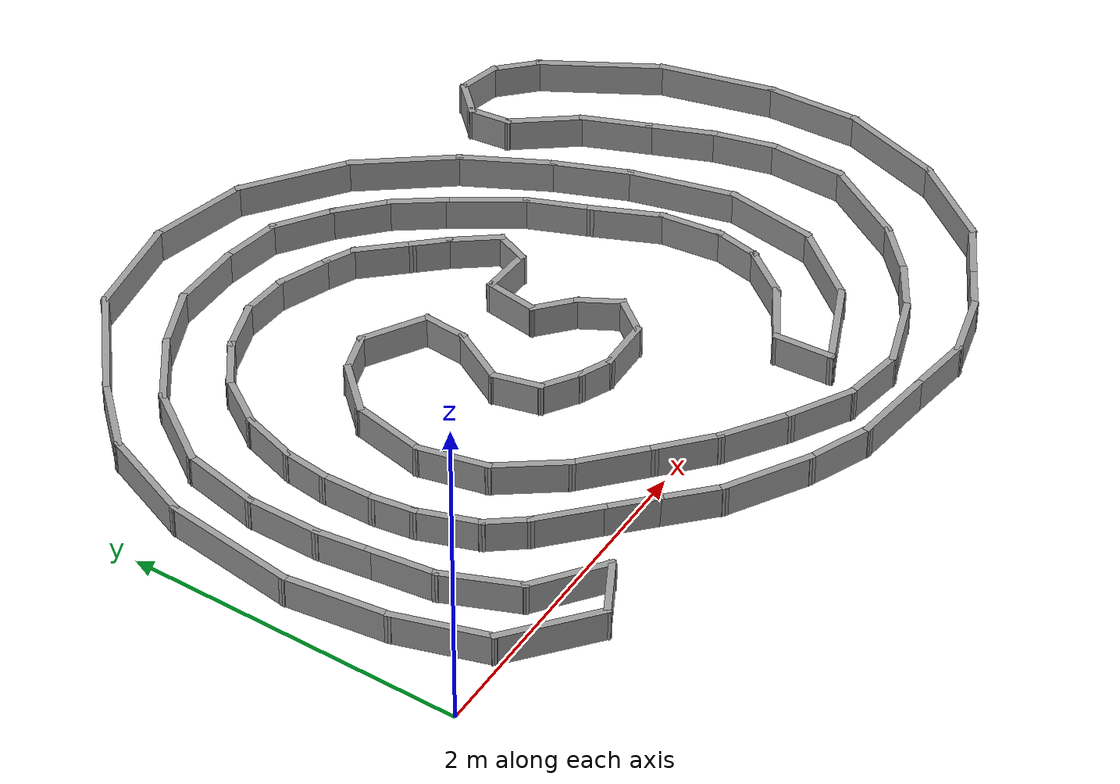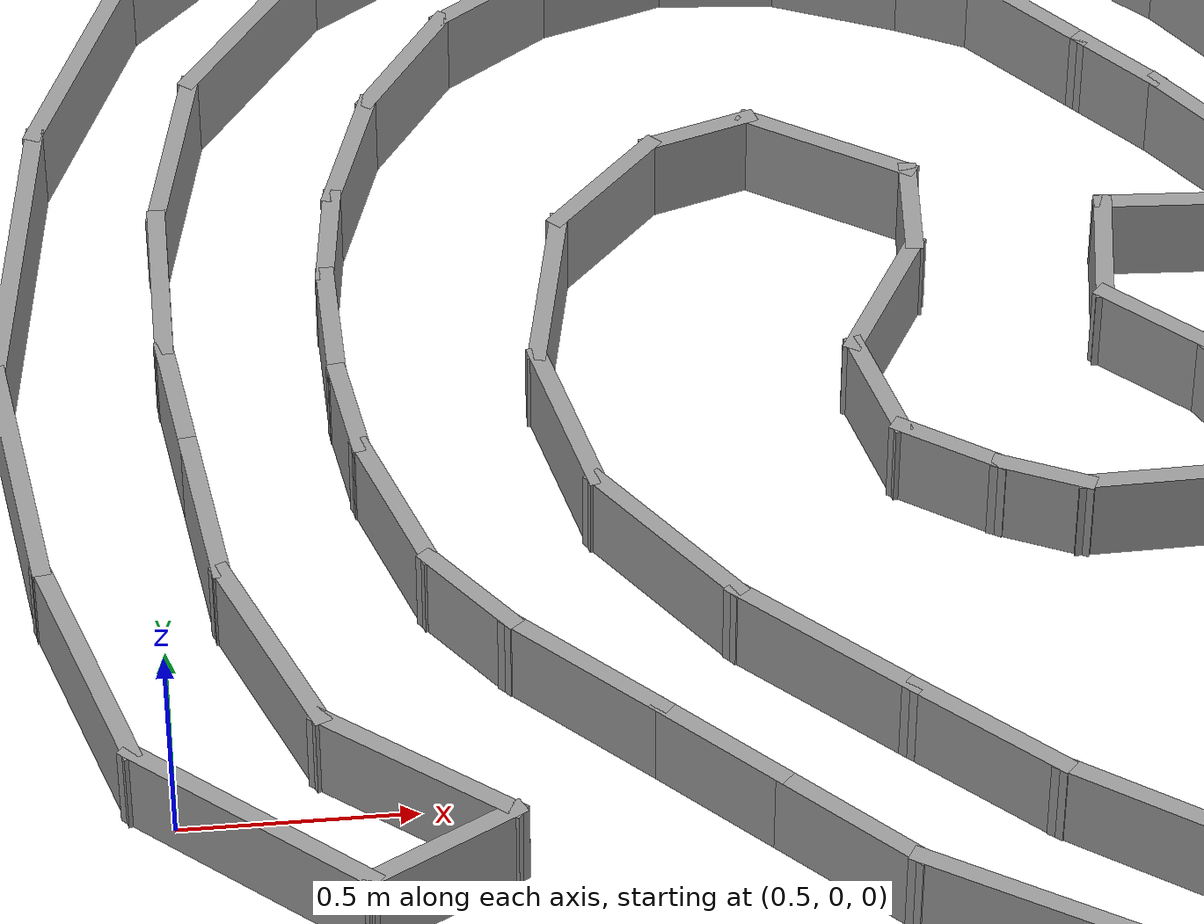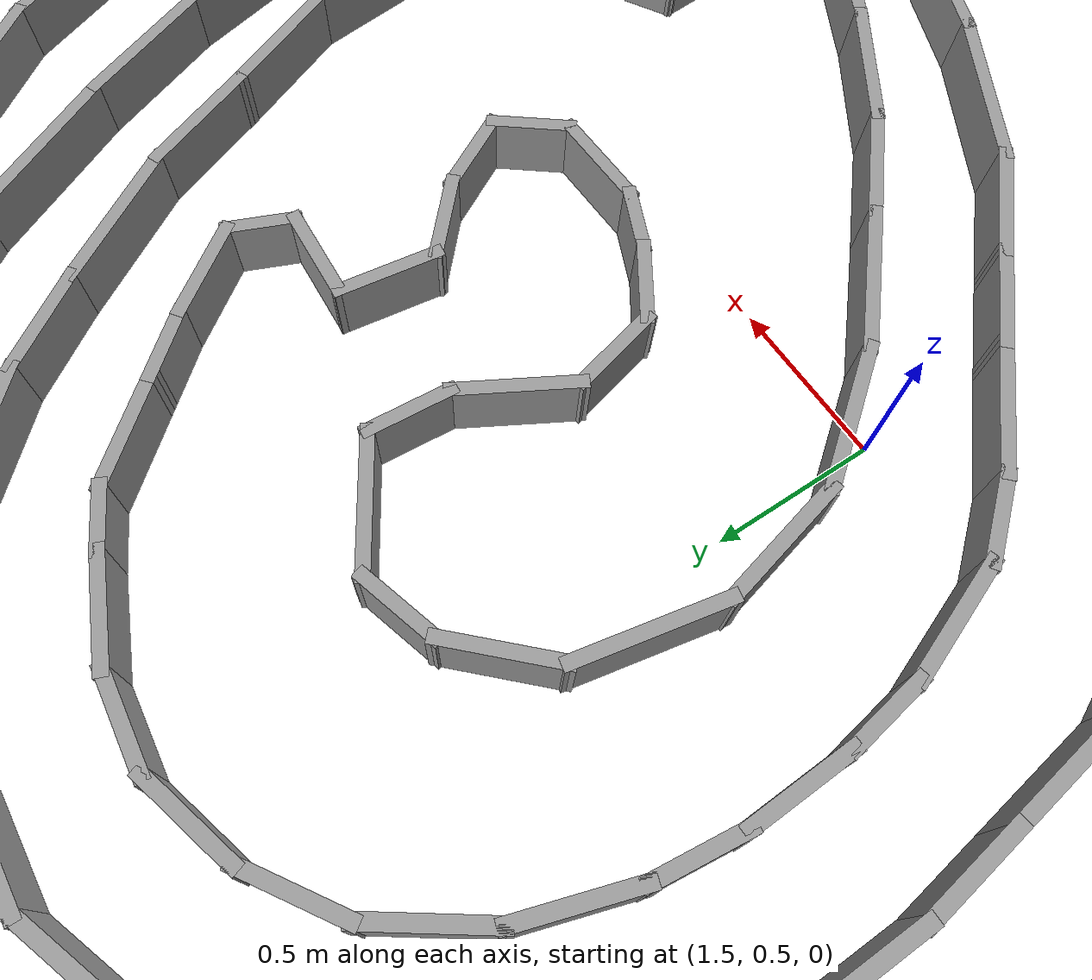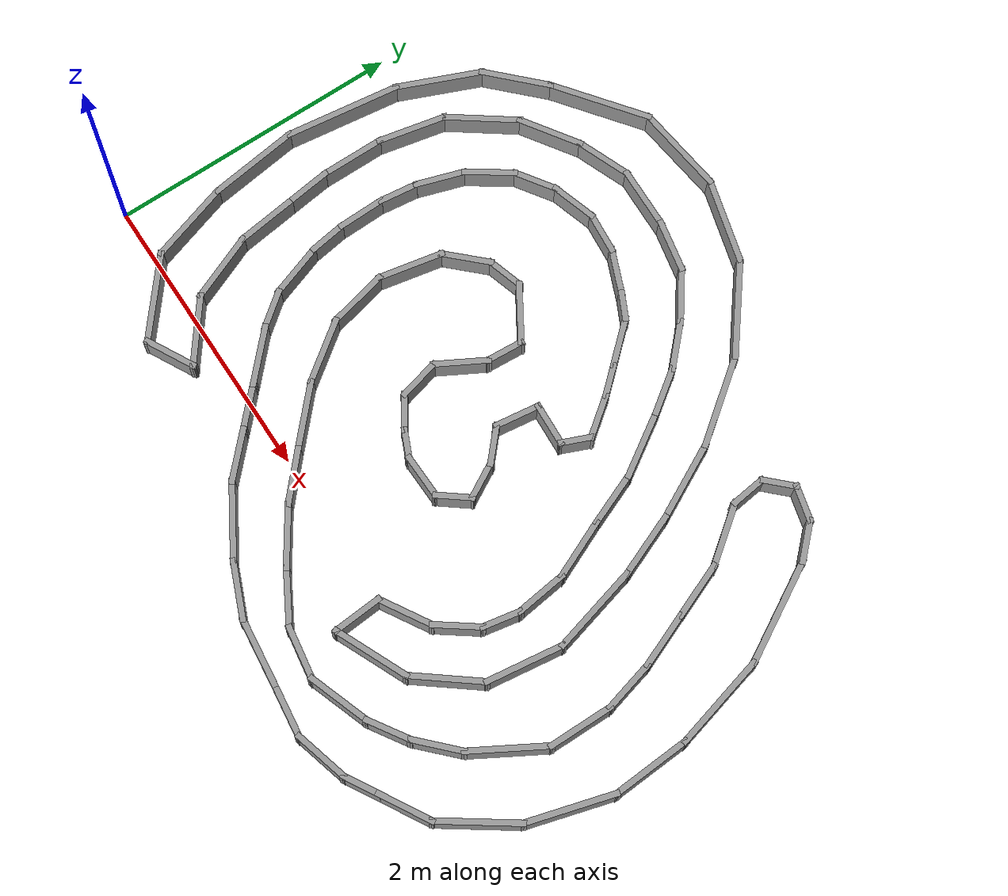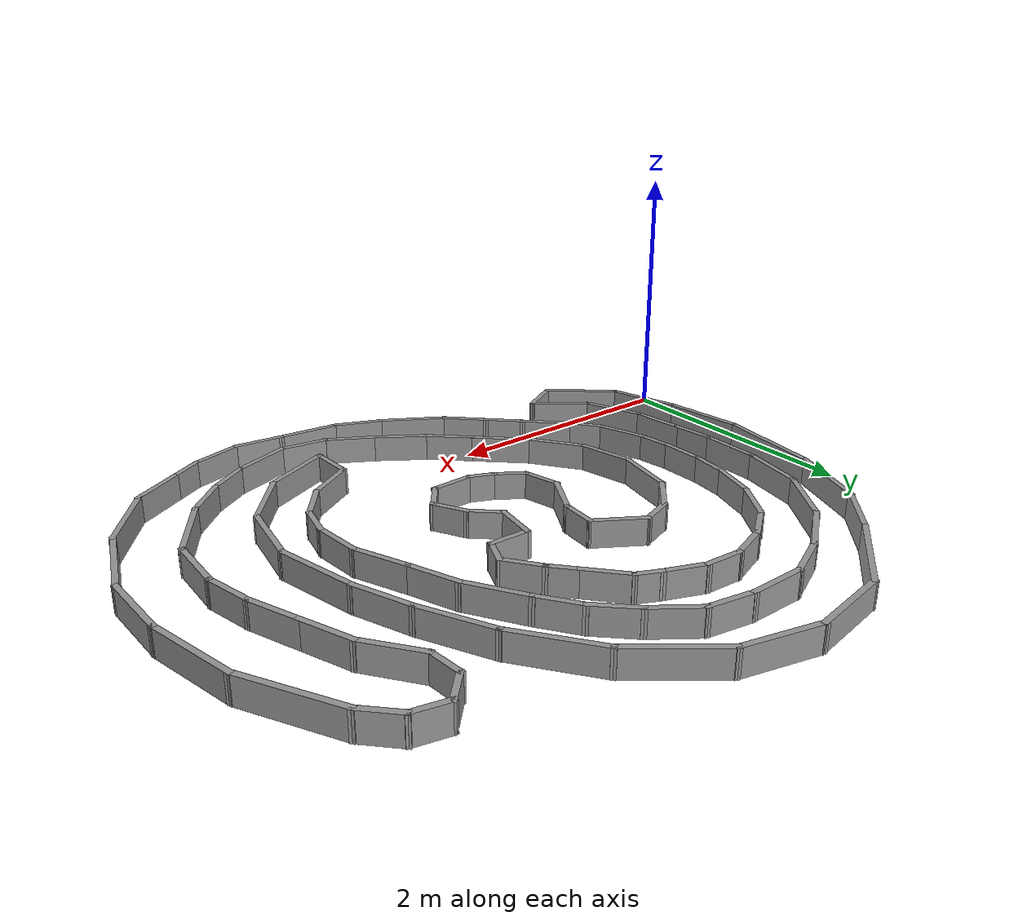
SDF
<?xml version='1.0'?>
<sdf version='1.4'>
  <model name='thymio_maze_large'>
    <link name='Wall_10'>
      <collision name='Wall_10_Collision'>
        <geometry>
          <box>
            <size>0.640228 0.04 0.2</size>
          </box>
        </geometry>
        <pose>0 0 0.1 0 -0 0</pose>
      </collision>
      <visual name='Wall_10_Visual'>
        <pose>0 0 0.1 0 -0 0</pose>
        <geometry>
          <box>
            <size>0.640228 0.04 0.2</size>
          </box>
        </geometry>
        <material>
          <script>
            <uri>file://media/materials/scripts/gazebo.material</uri>
            <name>Gazebo/Grey</name>
          </script>
        </material>
      </visual>
      <velocity_decay>
        <linear>0</linear>
        <angular>0</angular>
      </velocity_decay>
      <pose>1.65914 3.25351 0 0 -0 0.1309</pose>
    </link>
    <link name='Wall_100'>
      <collision name='Wall_100_Collision'>
        <geometry>
          <box>
            <size>0.22806 0.04 0.2</size>
          </box>
        </geometry>
        <pose>0 0 0.1 0 -0 0</pose>
      </collision>
      <visual name='Wall_100_Visual'>
        <pose>0 0 0.1 0 -0 0</pose>
        <geometry>
          <box>
            <size>0.22806 0.04 0.2</size>
          </box>
        </geometry>
        <material>
          <script>
            <uri>file://media/materials/scripts/gazebo.material</uri>
            <name>Gazebo/Grey</name>
          </script>
        </material>
      </visual>
      <velocity_decay>
        <linear>0</linear>
        <angular>0</angular>
      </velocity_decay>
      <pose>2.36575 0.672355 0 0 0 -0.415979</pose>
    </link>
    <link name='Wall_101'>
      <collision name='Wall_101_Collision'>
        <geometry>
          <box>
            <size>0.335749 0.04 0.2</size>
          </box>
        </geometry>
        <pose>0 0 0.1 0 -0 0</pose>
      </collision>
      <visual name='Wall_101_Visual'>
        <pose>0 0 0.1 0 -0 0</pose>
        <geometry>
          <box>
            <size>0.335749 0.04 0.2</size>
          </box>
        </geometry>
        <material>
          <script>
            <uri>file://media/materials/scripts/gazebo.material</uri>
            <name>Gazebo/Grey</name>
          </script>
        </material>
      </visual>
      <velocity_decay>
        <linear>0</linear>
        <angular>0</angular>
      </velocity_decay>
      <pose>2.59958 0.63814 0 0 -0 0.02557</pose>
    </link>
    <link name='Wall_102'>
      <collision name='Wall_102_Collision'>
        <geometry>
          <box>
            <size>0.271621 0.04 0.2</size>
          </box>
        </geometry>
        <pose>0 0 0.1 0 -0 0</pose>
      </collision>
      <visual name='Wall_102_Visual'>
        <pose>0 0 0.1 0 -0 0</pose>
        <geometry>
          <box>
            <size>0.271621 0.04 0.2</size>
          </box>
        </geometry>
        <material>
          <script>
            <uri>file://media/materials/scripts/gazebo.material</uri>
            <name>Gazebo/Grey</name>
          </script>
        </material>
      </visual>
      <velocity_decay>
        <linear>0</linear>
        <angular>0</angular>
      </velocity_decay>
      <pose>2.81792 0.733792 0 0 -0 0.916195</pose>
    </link>
    <link name='Wall_103'>
      <collision name='Wall_103_Collision'>
        <geometry>
          <box>
            <size>0.290702 0.04 0.2</size>
          </box>
        </geometry>
        <pose>0 0 0.1 0 -0 0</pose>
      </collision>
      <visual name='Wall_103_Visual'>
        <pose>0 0 0.1 0 -0 0</pose>
        <geometry>
          <box>
            <size>0.290702 0.04 0.2</size>
          </box>
        </geometry>
        <material>
          <script>
            <uri>file://media/materials/scripts/gazebo.material</uri>
            <name>Gazebo/Grey</name>
          </script>
        </material>
      </visual>
      <velocity_decay>
        <linear>0</linear>
        <angular>0</angular>
      </velocity_decay>
      <pose>2.827 0.934926 0 0 -0 2.08302</pose>
    </link>
    <link name='Wall_104'>
      <collision name='Wall_104_Collision'>
        <geometry>
          <box>
            <size>0.293396 0.04 0.2</size>
          </box>
        </geometry>
        <pose>0 0 0.1 0 -0 0</pose>
      </collision>
      <visual name='Wall_104_Visual'>
        <pose>0 0 0.1 0 -0 0</pose>
        <geometry>
          <box>
            <size>0.293396 0.04 0.2</size>
          </box>
        </geometry>
        <material>
          <script>
            <uri>file://media/materials/scripts/gazebo.material</uri>
            <name>Gazebo/Grey</name>
          </script>
        </material>
      </visual>
      <velocity_decay>
        <linear>0</linear>
        <angular>0</angular>
      </velocity_decay>
      <pose>2.67132 1.12915 0 0 -0 2.40792</pose>
    </link>
    <link name='Wall_105'>
      <collision name='Wall_105_Collision'>
        <geometry>
          <box>
            <size>0.335432 0.04 0.2</size>
          </box>
        </geometry>
        <pose>0 0 0.1 0 -0 0</pose>
      </collision>
      <visual name='Wall_105_Visual'>
        <pose>0 0 0.1 0 -0 0</pose>
        <geometry>
          <box>
            <size>0.335432 0.04 0.2</size>
          </box>
        </geometry>
        <material>
          <script>
            <uri>file://media/materials/scripts/gazebo.material</uri>
            <name>Gazebo/Grey</name>
          </script>
        </material>
      </visual>
      <velocity_decay>
        <linear>0</linear>
        <angular>0</angular>
      </velocity_decay>
      <pose>2.59631 1.36024 0 0 -0 1.4399</pose>
    </link>
    <link name='Wall_106'>
      <collision name='Wall_106_Collision'>
        <geometry>
          <box>
            <size>0.320937 0.04 0.2</size>
          </box>
        </geometry>
        <pose>0 0 0.1 0 -0 0</pose>
      </collision>
      <visual name='Wall_106_Visual'>
        <pose>0 0 0.1 0 -0 0</pose>
        <geometry>
          <box>
            <size>0.320937 0.04 0.2</size>
          </box>
        </geometry>
        <material>
          <script>
            <uri>file://media/materials/scripts/gazebo.material</uri>
            <name>Gazebo/Grey</name>
          </script>
        </material>
      </visual>
      <velocity_decay>
        <linear>0</linear>
        <angular>0</angular>
      </velocity_decay>
      <pose>2.75583 1.49919 0 0 0 -0.05102</pose>
    </link>
    <link name='Wall_107'>
      <collision name='Wall_107_Collision'>
        <geometry>
          <box>
            <size>0.236715 0.04 0.2</size>
          </box>
        </geometry>
        <pose>0 0 0.1 0 -0 0</pose>
      </collision>
      <visual name='Wall_107_Visual'>
        <pose>0 0 0.1 0 -0 0</pose>
        <geometry>
          <box>
            <size>0.236715 0.04 0.2</size>
          </box>
        </geometry>
        <material>
          <script>
            <uri>file://media/materials/scripts/gazebo.material</uri>
            <name>Gazebo/Grey</name>
          </script>
        </material>
      </visual>
      <velocity_decay>
        <linear>0</linear>
        <angular>0</angular>
      </velocity_decay>
      <pose>2.93376 1.5829 0 0 -0 1.1781</pose>
    </link>
    <link name='Wall_108'>
      <collision name='Wall_108_Collision'>
        <geometry>
          <box>
            <size>0.330495 0.04 0.2</size>
          </box>
        </geometry>
        <pose>0 0 0.1 0 -0 0</pose>
      </collision>
      <visual name='Wall_108_Visual'>
        <pose>0 0 0.1 0 -0 0</pose>
        <geometry>
          <box>
            <size>0.330495 0.04 0.2</size>
          </box>
        </geometry>
        <material>
          <script>
            <uri>file://media/materials/scripts/gazebo.material</uri>
            <name>Gazebo/Grey</name>
          </script>
        </material>
      </visual>
      <velocity_decay>
        <linear>0</linear>
        <angular>0</angular>
      </velocity_decay>
      <pose>2.88298 1.789 0 0 -0 2.2253</pose>
    </link>
    <link name='Wall_109'>
      <collision name='Wall_109_Collision'>
        <geometry>
          <box>
            <size>0.250362 0.04 0.2</size>
          </box>
        </geometry>
        <pose>0 0 0.1 0 -0 0</pose>
      </collision>
      <visual name='Wall_109_Visual'>
        <pose>0 0 0.1 0 -0 0</pose>
        <geometry>
          <box>
            <size>0.250362 0.04 0.2</size>
          </box>
        </geometry>
        <material>
          <script>
            <uri>file://media/materials/scripts/gazebo.material</uri>
            <name>Gazebo/Grey</name>
          </script>
        </material>
      </visual>
      <velocity_decay>
        <linear>0</linear>
        <angular>0</angular>
      </velocity_decay>
      <pose>2.72372 1.98215 0 0 -0 2.30861</pose>
    </link>
    <link name='Wall_11'>
      <collision name='Wall_11_Collision'>
        <geometry>
          <box>
            <size>0.612031 0.04 0.2</size>
          </box>
        </geometry>
        <pose>0 0 0.1 0 -0 0</pose>
      </collision>
      <visual name='Wall_11_Visual'>
        <pose>0 0 0.1 0 -0 0</pose>
        <geometry>
          <box>
            <size>0.612031 0.04 0.2</size>
          </box>
        </geometry>
        <material>
          <script>
            <uri>file://media/materials/scripts/gazebo.material</uri>
            <name>Gazebo/Grey</name>
          </script>
        </material>
      </visual>
      <velocity_decay>
        <linear>0</linear>
        <angular>0</angular>
      </velocity_decay>
      <pose>2.23278 3.21864 0 0 0 -0.261799</pose>
    </link>
    <link name='Wall_12'>
      <collision name='Wall_12_Collision'>
        <geometry>
          <box>
            <size>0.696371 0.04 0.2</size>
          </box>
        </geometry>
        <pose>0 0 0.1 0 -0 0</pose>
      </collision>
      <visual name='Wall_12_Visual'>
        <pose>0 0 0.1 0 -0 0</pose>
        <geometry>
          <box>
            <size>0.696371 0.04 0.2</size>
          </box>
        </geometry>
        <material>
          <script>
            <uri>file://media/materials/scripts/gazebo.material</uri>
            <name>Gazebo/Grey</name>
          </script>
        </material>
      </visual>
      <velocity_decay>
        <linear>0</linear>
        <angular>0</angular>
      </velocity_decay>
      <pose>2.76942 2.94482 0 0 0 -0.654498</pose>
    </link>
    <link name='Wall_13'>
      <collision name='Wall_13_Collision'>
        <geometry>
          <box>
            <size>0.665189 0.04 0.2</size>
          </box>
        </geometry>
        <pose>0 0 0.1 0 -0 0</pose>
      </collision>
      <visual name='Wall_13_Visual'>
        <pose>0 0 0.1 0 -0 0</pose>
        <geometry>
          <box>
            <size>0.665189 0.04 0.2</size>
          </box>
        </geometry>
        <material>
          <script>
            <uri>file://media/materials/scripts/gazebo.material</uri>
            <name>Gazebo/Grey</name>
          </script>
        </material>
      </visual>
      <velocity_decay>
        <linear>0</linear>
        <angular>0</angular>
      </velocity_decay>
      <pose>3.22022 2.49687 0 0 0 -0.916298</pose>
    </link>
    <link name='Wall_14'>
      <collision name='Wall_14_Collision'>
        <geometry>
          <box>
            <size>0.577995 0.04 0.2</size>
          </box>
        </geometry>
        <pose>0 0 0.1 0 -0 0</pose>
      </collision>
      <visual name='Wall_14_Visual'>
        <pose>0 0 0.1 0 -0 0</pose>
        <geometry>
          <box>
            <size>0.577995 0.04 0.2</size>
          </box>
        </geometry>
        <material>
          <script>
            <uri>file://media/materials/scripts/gazebo.material</uri>
            <name>Gazebo/Grey</name>
          </script>
        </material>
      </visual>
      <velocity_decay>
        <linear>0</linear>
        <angular>0</angular>
      </velocity_decay>
      <pose>3.53507 2.01022 0 0 0 -1.08988</pose>
    </link>
    <link name='Wall_15'>
      <collision name='Wall_15_Collision'>
        <geometry>
          <box>
            <size>0.479955 0.04 0.2</size>
          </box>
        </geometry>
        <pose>0 0 0.1 0 -0 0</pose>
      </collision>
      <visual name='Wall_15_Visual'>
        <pose>0 0 0.1 0 -0 0</pose>
        <geometry>
          <box>
            <size>0.479955 0.04 0.2</size>
          </box>
        </geometry>
        <material>
          <script>
            <uri>file://media/materials/scripts/gazebo.material</uri>
            <name>Gazebo/Grey</name>
          </script>
        </material>
      </visual>
      <velocity_decay>
        <linear>0</linear>
        <angular>0</angular>
      </velocity_decay>
      <pose>3.74369 1.5685 0 0 0 -1.1781</pose>
    </link>
    <link name='Wall_16'>
      <collision name='Wall_16_Collision'>
        <geometry>
          <box>
            <size>0.65013 0.04 0.2</size>
          </box>
        </geometry>
        <pose>0 0 0.1 0 -0 0</pose>
      </collision>
      <visual name='Wall_16_Visual'>
        <pose>0 0 0.1 0 -0 0</pose>
        <geometry>
          <box>
            <size>0.65013 0.04 0.2</size>
          </box>
        </geometry>
        <material>
          <script>
            <uri>file://media/materials/scripts/gazebo.material</uri>
            <name>Gazebo/Grey</name>
          </script>
        </material>
      </visual>
      <velocity_decay>
        <linear>0</linear>
        <angular>0</angular>
      </velocity_decay>
      <pose>3.90683 1.0706 0 0 0 -1.309</pose>
    </link>
    <link name='Wall_17'>
      <collision name='Wall_17_Collision'>
        <geometry>
          <box>
            <size>0.56326 0.04 0.2</size>
          </box>
        </geometry>
        <pose>0 0 0.1 0 -0 0</pose>
      </collision>
      <visual name='Wall_17_Visual'>
        <pose>0 0 0.1 0 -0 0</pose>
        <geometry>
          <box>
            <size>0.56326 0.04 0.2</size>
          </box>
        </geometry>
        <material>
          <script>
            <uri>file://media/materials/scripts/gazebo.material</uri>
            <name>Gazebo/Grey</name>
          </script>
        </material>
      </visual>
      <velocity_decay>
        <linear>0</linear>
        <angular>0</angular>
      </velocity_decay>
      <pose>3.95161 0.516304 0 0 0 -1.7017</pose>
    </link>
    <link name='Wall_18'>
      <collision name='Wall_18_Collision'>
        <geometry>
          <box>
            <size>0.539122 0.04 0.2</size>
          </box>
        </geometry>
        <pose>0 0 0.1 0 -0 0</pose>
      </collision>
      <visual name='Wall_18_Visual'>
        <pose>0 0 0.1 0 -0 0</pose>
        <geometry>
          <box>
            <size>0.539122 0.04 0.2</size>
          </box>
        </geometry>
        <material>
          <script>
            <uri>file://media/materials/scripts/gazebo.material</uri>
            <name>Gazebo/Grey</name>
          </script>
        </material>
      </visual>
      <velocity_decay>
        <linear>0</linear>
        <angular>0</angular>
      </velocity_decay>
      <pose>3.76444 0.05951 0 0 0 -2.23066</pose>
    </link>
    <link name='Wall_19'>
      <collision name='Wall_19_Collision'>
        <geometry>
          <box>
            <size>0.559261 0.04 0.2</size>
          </box>
        </geometry>
        <pose>0 0 0.1 0 -0 0</pose>
      </collision>
      <visual name='Wall_19_Visual'>
        <pose>0 0 0.1 0 -0 0</pose>
        <geometry>
          <box>
            <size>0.559261 0.04 0.2</size>
          </box>
        </geometry>
        <material>
          <script>
            <uri>file://media/materials/scripts/gazebo.material</uri>
            <name>Gazebo/Grey</name>
          </script>
        </material>
      </visual>
      <velocity_decay>
        <linear>0</linear>
        <angular>0</angular>
      </velocity_decay>
      <pose>3.3743 -0.243309 0 0 0 -2.72252</pose>
    </link>
    <link name='Wall_20'>
      <collision name='Wall_20_Collision'>
        <geometry>
          <box>
            <size>0.368009 0.04 0.2</size>
          </box>
        </geometry>
        <pose>0 0 0.1 0 -0 0</pose>
      </collision>
      <visual name='Wall_20_Visual'>
        <pose>0 0 0.1 0 -0 0</pose>
        <geometry>
          <box>
            <size>0.368009 0.04 0.2</size>
          </box>
        </geometry>
        <material>
          <script>
            <uri>file://media/materials/scripts/gazebo.material</uri>
            <name>Gazebo/Grey</name>
          </script>
        </material>
      </visual>
      <velocity_decay>
        <linear>0</linear>
        <angular>0</angular>
      </velocity_decay>
      <pose>3.12477 -0.18542 0 0 -0 1.64626</pose>
    </link>
    <link name='Wall_21'>
      <collision name='Wall_21_Collision'>
        <geometry>
          <box>
            <size>0.412007 0.04 0.2</size>
          </box>
        </geometry>
        <pose>0 0 0.1 0 -0 0</pose>
      </collision>
      <visual name='Wall_21_Visual'>
        <pose>0 0 0.1 0 -0 0</pose>
        <geometry>
          <box>
            <size>0.412007 0.04 0.2</size>
          </box>
        </geometry>
        <material>
          <script>
            <uri>file://media/materials/scripts/gazebo.material</uri>
            <name>Gazebo/Grey</name>
          </script>
        </material>
      </visual>
      <velocity_decay>
        <linear>0</linear>
        <angular>0</angular>
      </velocity_decay>
      <pose>3.27176 0.074045 0 0 -0 0.541856</pose>
    </link>
    <link name='Wall_22'>
      <collision name='Wall_22_Collision'>
        <geometry>
          <box>
            <size>0.355008 0.04 0.2</size>
          </box>
        </geometry>
        <pose>0 0 0.1 0 -0 0</pose>
      </collision>
      <visual name='Wall_22_Visual'>
        <pose>0 0 0.1 0 -0 0</pose>
        <geometry>
          <box>
            <size>0.355008 0.04 0.2</size>
          </box>
        </geometry>
        <material>
          <script>
            <uri>file://media/materials/scripts/gazebo.material</uri>
            <name>Gazebo/Grey</name>
          </script>
        </material>
      </visual>
      <velocity_decay>
        <linear>0</linear>
        <angular>0</angular>
      </velocity_decay>
      <pose>3.5239 0.29725 0 0 -0 0.94091</pose>
    </link>
    <link name='Wall_23'>
      <collision name='Wall_23_Collision'>
        <geometry>
          <box>
            <size>0.291039 0.04 0.2</size>
          </box>
        </geometry>
        <pose>0 0 0.1 0 -0 0</pose>
      </collision>
      <visual name='Wall_23_Visual'>
        <pose>0 0 0.1 0 -0 0</pose>
        <geometry>
          <box>
            <size>0.291039 0.04 0.2</size>
          </box>
        </geometry>
        <material>
          <script>
            <uri>file://media/materials/scripts/gazebo.material</uri>
            <name>Gazebo/Grey</name>
          </script>
        </material>
      </visual>
      <velocity_decay>
        <linear>0</linear>
        <angular>0</angular>
      </velocity_decay>
      <pose>3.63941 0.547973 0 0 -0 1.38871</pose>
    </link>
    <link name='Wall_24'>
      <collision name='Wall_24_Collision'>
        <geometry>
          <box>
            <size>0.388273 0.04 0.2</size>
          </box>
        </geometry>
        <pose>0 0 0.1 0 -0 0</pose>
      </collision>
      <visual name='Wall_24_Visual'>
        <pose>0 0 0.1 0 -0 0</pose>
        <geometry>
          <box>
            <size>0.388273 0.04 0.2</size>
          </box>
        </geometry>
        <material>
          <script>
            <uri>file://media/materials/scripts/gazebo.material</uri>
            <name>Gazebo/Grey</name>
          </script>
        </material>
      </visual>
      <velocity_decay>
        <linear>0</linear>
        <angular>0</angular>
      </velocity_decay>
      <pose>3.63941 0.844064 0 0 -0 1.7017</pose>
    </link>
    <link name='Wall_25'>
      <collision name='Wall_25_Collision'>
        <geometry>
          <box>
            <size>0.449048 0.04 0.2</size>
          </box>
        </geometry>
        <pose>0 0 0.1 0 -0 0</pose>
      </collision>
      <visual name='Wall_25_Visual'>
        <pose>0 0 0.1 0 -0 0</pose>
        <geometry>
          <box>
            <size>0.449048 0.04 0.2</size>
          </box>
        </geometry>
        <material>
          <script>
            <uri>file://media/materials/scripts/gazebo.material</uri>
            <name>Gazebo/Grey</name>
          </script>
        </material>
      </visual>
      <velocity_decay>
        <linear>0</linear>
        <angular>0</angular>
      </velocity_decay>
      <pose>3.53342 1.20363 0 0 -0 1.98985</pose>
    </link>
    <link name='Wall_26'>
      <collision name='Wall_26_Collision'>
        <geometry>
          <box>
            <size>0.405797 0.04 0.2</size>
          </box>
        </geometry>
        <pose>0 0 0.1 0 -0 0</pose>
      </collision>
      <visual name='Wall_26_Visual'>
        <pose>0 0 0.1 0 -0 0</pose>
        <geometry>
          <box>
            <size>0.405797 0.04 0.2</size>
          </box>
        </geometry>
        <material>
          <script>
            <uri>file://media/materials/scripts/gazebo.material</uri>
            <name>Gazebo/Grey</name>
          </script>
        </material>
      </visual>
      <velocity_decay>
        <linear>0</linear>
        <angular>0</angular>
      </velocity_decay>
      <pose>3.38016 1.55953 0 0 -0 1.96349</pose>
    </link>
    <link name='Wall_27'>
      <collision name='Wall_27_Collision'>
        <geometry>
          <box>
            <size>0.493405 0.04 0.2</size>
          </box>
        </geometry>
        <pose>0 0 0.1 0 -0 0</pose>
      </collision>
      <visual name='Wall_27_Visual'>
        <pose>0 0 0.1 0 -0 0</pose>
        <geometry>
          <box>
            <size>0.493405 0.04 0.2</size>
          </box>
        </geometry>
        <material>
          <script>
            <uri>file://media/materials/scripts/gazebo.material</uri>
            <name>Gazebo/Grey</name>
          </script>
        </material>
      </visual>
      <velocity_decay>
        <linear>0</linear>
        <angular>0</angular>
      </velocity_decay>
      <pose>3.18649 1.9185 0 0 -0 2.14783</pose>
    </link>
    <link name='Wall_28'>
      <collision name='Wall_28_Collision'>
        <geometry>
          <box>
            <size>0.352834 0.04 0.2</size>
          </box>
        </geometry>
        <pose>0 0 0.1 0 -0 0</pose>
      </collision>
      <visual name='Wall_28_Visual'>
        <pose>0 0 0.1 0 -0 0</pose>
        <geometry>
          <box>
            <size>0.352834 0.04 0.2</size>
          </box>
        </geometry>
        <material>
          <script>
            <uri>file://media/materials/scripts/gazebo.material</uri>
            <name>Gazebo/Grey</name>
          </script>
        </material>
      </visual>
      <velocity_decay>
        <linear>0</linear>
        <angular>0</angular>
      </velocity_decay>
      <pose>2.97082 2.235 0 0 -0 2.19959</pose>
    </link>
    <link name='Wall_29'>
      <collision name='Wall_29_Collision'>
        <geometry>
          <box>
            <size>0.36669 0.04 0.2</size>
          </box>
        </geometry>
        <pose>0 0 0.1 0 -0 0</pose>
      </collision>
      <visual name='Wall_29_Visual'>
        <pose>0 0 0.1 0 -0 0</pose>
        <geometry>
          <box>
            <size>0.36669 0.04 0.2</size>
          </box>
        </geometry>
        <material>
          <script>
            <uri>file://media/materials/scripts/gazebo.material</uri>
            <name>Gazebo/Grey</name>
          </script>
        </material>
      </visual>
      <velocity_decay>
        <linear>0</linear>
        <angular>0</angular>
      </velocity_decay>
      <pose>2.7604 2.47402 0 0 -0 2.38174</pose>
    </link>
    <link name='Wall_3'>
      <collision name='Wall_3_Collision'>
        <geometry>
          <box>
            <size>0.64059 0.04 0.2</size>
          </box>
        </geometry>
        <pose>0 0 0.1 0 -0 0</pose>
      </collision>
      <visual name='Wall_3_Visual'>
        <pose>0 0 0.1 0 -0 0</pose>
        <geometry>
          <box>
            <size>0.64059 0.04 0.2</size>
          </box>
        </geometry>
        <material>
          <script>
            <uri>file://media/materials/scripts/gazebo.material</uri>
            <name>Gazebo/Grey</name>
          </script>
        </material>
      </visual>
      <velocity_decay>
        <linear>0</linear>
        <angular>0</angular>
      </velocity_decay>
      <pose>0.650699 -0.152621 0 0 -0 2.44735</pose>
    </link>
    <link name='Wall_30'>
      <collision name='Wall_30_Collision'>
        <geometry>
          <box>
            <size>0.397703 0.04 0.2</size>
          </box>
        </geometry>
        <pose>0 0 0.1 0 -0 0</pose>
      </collision>
      <visual name='Wall_30_Visual'>
        <pose>0 0 0.1 0 -0 0</pose>
        <geometry>
          <box>
            <size>0.397703 0.04 0.2</size>
          </box>
        </geometry>
        <material>
          <script>
            <uri>file://media/materials/scripts/gazebo.material</uri>
            <name>Gazebo/Grey</name>
          </script>
        </material>
      </visual>
      <velocity_decay>
        <linear>0</linear>
        <angular>0</angular>
      </velocity_decay>
      <pose>2.49668 2.69081 0 0 -0 2.51912</pose>
    </link>
    <link name='Wall_31'>
      <collision name='Wall_31_Collision'>
        <geometry>
          <box>
            <size>0.377767 0.04 0.2</size>
          </box>
        </geometry>
        <pose>0 0 0.1 0 -0 0</pose>
      </collision>
      <visual name='Wall_31_Visual'>
        <pose>0 0 0.1 0 -0 0</pose>
        <geometry>
          <box>
            <size>0.377767 0.04 0.2</size>
          </box>
        </geometry>
        <material>
          <script>
            <uri>file://media/materials/scripts/gazebo.material</uri>
            <name>Gazebo/Grey</name>
          </script>
        </material>
      </visual>
      <velocity_decay>
        <linear>0</linear>
        <angular>0</angular>
      </velocity_decay>
      <pose>2.18571 2.82788 0 0 -0 2.94618</pose>
    </link>
    <link name='Wall_32'>
      <collision name='Wall_32_Collision'>
        <geometry>
          <box>
            <size>0.445946 0.04 0.2</size>
          </box>
        </geometry>
        <pose>0 0 0.1 0 -0 0</pose>
      </collision>
      <visual name='Wall_32_Visual'>
        <pose>0 0 0.1 0 -0 0</pose>
        <geometry>
          <box>
            <size>0.445946 0.04 0.2</size>
          </box>
        </geometry>
        <material>
          <script>
            <uri>file://media/materials/scripts/gazebo.material</uri>
            <name>Gazebo/Grey</name>
          </script>
        </material>
      </visual>
      <velocity_decay>
        <linear>0</linear>
        <angular>0</angular>
      </velocity_decay>
      <pose>1.81708 2.86564 0 0 -0 3.1171</pose>
    </link>
    <link name='Wall_33'>
      <collision name='Wall_33_Collision'>
        <geometry>
          <box>
            <size>0.408855 0.04 0.2</size>
          </box>
        </geometry>
        <pose>0 0 0.1 0 -0 0</pose>
      </collision>
      <visual name='Wall_33_Visual'>
        <pose>0 0 0.1 0 -0 0</pose>
        <geometry>
          <box>
            <size>0.408855 0.04 0.2</size>
          </box>
        </geometry>
        <material>
          <script>
            <uri>file://media/materials/scripts/gazebo.material</uri>
            <name>Gazebo/Grey</name>
          </script>
        </material>
      </visual>
      <velocity_decay>
        <linear>0</linear>
        <angular>0</angular>
      </velocity_decay>
      <pose>1.44303 2.80176 0 0 0 -2.75902</pose>
    </link>
    <link name='Wall_34'>
      <collision name='Wall_34_Collision'>
        <geometry>
          <box>
            <size>0.46591 0.04 0.2</size>
          </box>
        </geometry>
        <pose>0 0 0.1 0 -0 0</pose>
      </collision>
      <visual name='Wall_34_Visual'>
        <pose>0 0 0.1 0 -0 0</pose>
        <geometry>
          <box>
            <size>0.46591 0.04 0.2</size>
          </box>
        </geometry>
        <material>
          <script>
            <uri>file://media/materials/scripts/gazebo.material</uri>
            <name>Gazebo/Grey</name>
          </script>
        </material>
      </visual>
      <velocity_decay>
        <linear>0</linear>
        <angular>0</angular>
      </velocity_decay>
      <pose>1.09545 2.61374 0 0 0 -2.54765</pose>
    </link>
    <link name='Wall_35'>
      <collision name='Wall_35_Collision'>
        <geometry>
          <box>
            <size>0.537216 0.04 0.2</size>
          </box>
        </geometry>
        <pose>0 0 0.1 0 -0 0</pose>
      </collision>
      <visual name='Wall_35_Visual'>
        <pose>0 0 0.1 0 -0 0</pose>
        <geometry>
          <box>
            <size>0.537216 0.04 0.2</size>
          </box>
        </geometry>
        <material>
          <script>
            <uri>file://media/materials/scripts/gazebo.material</uri>
            <name>Gazebo/Grey</name>
          </script>
        </material>
      </visual>
      <velocity_decay>
        <linear>0</linear>
        <angular>0</angular>
      </velocity_decay>
      <pose>0.773701 2.29281 0 0 0 -2.19482</pose>
    </link>
    <link name='Wall_36'>
      <collision name='Wall_36_Collision'>
        <geometry>
          <box>
            <size>0.496142 0.04 0.2</size>
          </box>
        </geometry>
        <pose>0 0 0.1 0 -0 0</pose>
      </collision>
      <visual name='Wall_36_Visual'>
        <pose>0 0 0.1 0 -0 0</pose>
        <geometry>
          <box>
            <size>0.496142 0.04 0.2</size>
          </box>
        </geometry>
        <material>
          <script>
            <uri>file://media/materials/scripts/gazebo.material</uri>
            <name>Gazebo/Grey</name>
          </script>
        </material>
      </visual>
      <velocity_decay>
        <linear>0</linear>
        <angular>0</angular>
      </velocity_decay>
      <pose>0.581968 1.86777 0 0 0 -1.77599</pose>
    </link>
    <link name='Wall_37'>
      <collision name='Wall_37_Collision'>
        <geometry>
          <box>
            <size>0.464137 0.04 0.2</size>
          </box>
        </geometry>
        <pose>0 0 0.1 0 -0 0</pose>
      </collision>
      <visual name='Wall_37_Visual'>
        <pose>0 0 0.1 0 -0 0</pose>
        <geometry>
          <box>
            <size>0.464137 0.04 0.2</size>
          </box>
        </geometry>
        <material>
          <script>
            <uri>file://media/materials/scripts/gazebo.material</uri>
            <name>Gazebo/Grey</name>
          </script>
        </material>
      </visual>
      <velocity_decay>
        <linear>0</linear>
        <angular>0</angular>
      </velocity_decay>
      <pose>0.535498 1.43241 0 0 0 -1.5708</pose>
    </link>
    <link name='Wall_38'>
      <collision name='Wall_38_Collision'>
        <geometry>
          <box>
            <size>0.344538 0.04 0.2</size>
          </box>
        </geometry>
        <pose>0 0 0.1 0 -0 0</pose>
      </collision>
      <visual name='Wall_38_Visual'>
        <pose>0 0 0.1 0 -0 0</pose>
        <geometry>
          <box>
            <size>0.344538 0.04 0.2</size>
          </box>
        </geometry>
        <material>
          <script>
            <uri>file://media/materials/scripts/gazebo.material</uri>
            <name>Gazebo/Grey</name>
          </script>
        </material>
      </visual>
      <velocity_decay>
        <linear>0</linear>
        <angular>0</angular>
      </velocity_decay>
      <pose>0.555346 1.06958 0 0 0 -1.4399</pose>
    </link>
    <link name='Wall_39'>
      <collision name='Wall_39_Collision'>
        <geometry>
          <box>
            <size>0.426425 0.04 0.2</size>
          </box>
        </geometry>
        <pose>0 0 0.1 0 -0 0</pose>
      </collision>
      <visual name='Wall_39_Visual'>
        <pose>0 0 0.1 0 -0 0</pose>
        <geometry>
          <box>
            <size>0.426425 0.04 0.2</size>
          </box>
        </geometry>
        <material>
          <script>
            <uri>file://media/materials/scripts/gazebo.material</uri>
            <name>Gazebo/Grey</name>
          </script>
        </material>
      </visual>
      <velocity_decay>
        <linear>0</linear>
        <angular>0</angular>
      </velocity_decay>
      <pose>0.600447 0.727005 0 0 0 -1.4399</pose>
    </link>
    <link name='Wall_4'>
      <collision name='Wall_4_Collision'>
        <geometry>
          <box>
            <size>0.599597 0.04 0.2</size>
          </box>
        </geometry>
        <pose>0 0 0.1 0 -0 0</pose>
      </collision>
      <visual name='Wall_4_Visual'>
        <pose>0 0 0.1 0 -0 0</pose>
        <geometry>
          <box>
            <size>0.599597 0.04 0.2</size>
          </box>
        </geometry>
        <material>
          <script>
            <uri>file://media/materials/scripts/gazebo.material</uri>
            <name>Gazebo/Grey</name>
          </script>
        </material>
      </visual>
      <velocity_decay>
        <linear>0</linear>
        <angular>0</angular>
      </velocity_decay>
      <pose>0.336794 0.306676 0 0 -0 1.87241</pose>
    </link>
    <link name='Wall_40'>
      <collision name='Wall_40_Collision'>
        <geometry>
          <box>
            <size>0.508927 0.04 0.2</size>
          </box>
        </geometry>
        <pose>0 0 0.1 0 -0 0</pose>
      </collision>
      <visual name='Wall_40_Visual'>
        <pose>0 0 0.1 0 -0 0</pose>
        <geometry>
          <box>
            <size>0.508927 0.04 0.2</size>
          </box>
        </geometry>
        <material>
          <script>
            <uri>file://media/materials/scripts/gazebo.material</uri>
            <name>Gazebo/Grey</name>
          </script>
        </material>
      </visual>
      <velocity_decay>
        <linear>0</linear>
        <angular>0</angular>
      </velocity_decay>
      <pose>0.715425 0.318573 0 0 0 -1.1781</pose>
    </link>
    <link name='Wall_41'>
      <collision name='Wall_41_Collision'>
        <geometry>
          <box>
            <size>0.51206 0.04 0.2</size>
          </box>
        </geometry>
        <pose>0 0 0.1 0 -0 0</pose>
      </collision>
      <visual name='Wall_41_Visual'>
        <pose>0 0 0.1 0 -0 0</pose>
        <geometry>
          <box>
            <size>0.51206 0.04 0.2</size>
          </box>
        </geometry>
        <material>
          <script>
            <uri>file://media/materials/scripts/gazebo.material</uri>
            <name>Gazebo/Grey</name>
          </script>
        </material>
      </visual>
      <velocity_decay>
        <linear>0</linear>
        <angular>0</angular>
      </velocity_decay>
      <pose>0.992405 -0.041729 0 0 0 -0.654498</pose>
    </link>
    <link name='Wall_42'>
      <collision name='Wall_42_Collision'>
        <geometry>
          <box>
            <size>0.378075 0.04 0.2</size>
          </box>
        </geometry>
        <pose>0 0 0.1 0 -0 0</pose>
      </collision>
      <visual name='Wall_42_Visual'>
        <pose>0 0 0.1 0 -0 0</pose>
        <geometry>
          <box>
            <size>0.378075 0.04 0.2</size>
          </box>
        </geometry>
        <material>
          <script>
            <uri>file://media/materials/scripts/gazebo.material</uri>
            <name>Gazebo/Grey</name>
          </script>
        </material>
      </visual>
      <velocity_decay>
        <linear>0</linear>
        <angular>0</angular>
      </velocity_decay>
      <pose>1.03057 -0.265082 0 0 0 -2.65083</pose>
    </link>
    <link name='Wall_44'>
      <collision name='Wall_44_Collision'>
        <geometry>
          <box>
            <size>0.365477 0.04 0.2</size>
          </box>
        </geometry>
        <pose>0 0 0.1 0 -0 0</pose>
      </collision>
      <visual name='Wall_44_Visual'>
        <pose>0 0 0.1 0 -0 0</pose>
        <geometry>
          <box>
            <size>0.365477 0.04 0.2</size>
          </box>
        </geometry>
        <material>
          <script>
            <uri>file://media/materials/scripts/gazebo.material</uri>
            <name>Gazebo/Grey</name>
          </script>
        </material>
      </visual>
      <velocity_decay>
        <linear>0</linear>
        <angular>0</angular>
      </velocity_decay>
      <pose>2.54363 2.18067 0 0 -0 2.30689</pose>
    </link>
    <link name='Wall_45'>
      <collision name='Wall_45_Collision'>
        <geometry>
          <box>
            <size>0.21552 0.04 0.2</size>
          </box>
        </geometry>
        <pose>0 0 0.1 0 -0 0</pose>
      </collision>
      <visual name='Wall_45_Visual'>
        <pose>0 0 0.1 0 -0 0</pose>
        <geometry>
          <box>
            <size>0.21552 0.04 0.2</size>
          </box>
        </geometry>
        <material>
          <script>
            <uri>file://media/materials/scripts/gazebo.material</uri>
            <name>Gazebo/Grey</name>
          </script>
        </material>
      </visual>
      <velocity_decay>
        <linear>0</linear>
        <angular>0</angular>
      </velocity_decay>
      <pose>2.35535 2.33946 0 0 -0 2.69143</pose>
    </link>
    <link name='Wall_46'>
      <collision name='Wall_46_Collision'>
        <geometry>
          <box>
            <size>0.340346 0.04 0.2</size>
          </box>
        </geometry>
        <pose>0 0 0.1 0 -0 0</pose>
      </collision>
      <visual name='Wall_46_Visual'>
        <pose>0 0 0.1 0 -0 0</pose>
        <geometry>
          <box>
            <size>0.340346 0.04 0.2</size>
          </box>
        </geometry>
        <material>
          <script>
            <uri>file://media/materials/scripts/gazebo.material</uri>
            <name>Gazebo/Grey</name>
          </script>
        </material>
      </visual>
      <velocity_decay>
        <linear>0</linear>
        <angular>0</angular>
      </velocity_decay>
      <pose>2.1372 2.43417 0 0 -0 2.75571</pose>
    </link>
    <link name='Wall_47'>
      <collision name='Wall_47_Collision'>
        <geometry>
          <box>
            <size>0.309003 0.04 0.2</size>
          </box>
        </geometry>
        <pose>0 0 0.1 0 -0 0</pose>
      </collision>
      <visual name='Wall_47_Visual'>
        <pose>0 0 0.1 0 -0 0</pose>
        <geometry>
          <box>
            <size>0.309003 0.04 0.2</size>
          </box>
        </geometry>
        <material>
          <script>
            <uri>file://media/materials/scripts/gazebo.material</uri>
            <name>Gazebo/Grey</name>
          </script>
        </material>
      </visual>
      <velocity_decay>
        <linear>0</linear>
        <angular>0</angular>
      </velocity_decay>
      <pose>1.86442 2.50203 0 0 -0 3.05693</pose>
    </link>
    <link name='Wall_48'>
      <collision name='Wall_48_Collision'>
        <geometry>
          <box>
            <size>0.337261 0.04 0.2</size>
          </box>
        </geometry>
        <pose>0 0 0.1 0 -0 0</pose>
      </collision>
      <visual name='Wall_48_Visual'>
        <pose>0 0 0.1 0 -0 0</pose>
        <geometry>
          <box>
            <size>0.337261 0.04 0.2</size>
          </box>
        </geometry>
        <material>
          <script>
            <uri>file://media/materials/scripts/gazebo.material</uri>
            <name>Gazebo/Grey</name>
          </script>
        </material>
      </visual>
      <velocity_decay>
        <linear>0</linear>
        <angular>0</angular>
      </velocity_decay>
      <pose>1.589 2.46876 0 0 0 -2.83674</pose>
    </link>
    <link name='Wall_49'>
      <collision name='Wall_49_Collision'>
        <geometry>
          <box>
            <size>0.328591 0.04 0.2</size>
          </box>
        </geometry>
        <pose>0 0 0.1 0 -0 0</pose>
      </collision>
      <visual name='Wall_49_Visual'>
        <pose>0 0 0.1 0 -0 0</pose>
        <geometry>
          <box>
            <size>0.328591 0.04 0.2</size>
          </box>
        </geometry>
        <material>
          <script>
            <uri>file://media/materials/scripts/gazebo.material</uri>
            <name>Gazebo/Grey</name>
          </script>
        </material>
      </visual>
      <velocity_decay>
        <linear>0</linear>
        <angular>0</angular>
      </velocity_decay>
      <pose>1.32813 2.34268 0 0 0 -2.5416</pose>
    </link>
    <link name='Wall_5'>
      <collision name='Wall_5_Collision'>
        <geometry>
          <box>
            <size>0.645624 0.04 0.2</size>
          </box>
        </geometry>
        <pose>0 0 0.1 0 -0 0</pose>
      </collision>
      <visual name='Wall_5_Visual'>
        <pose>0 0 0.1 0 -0 0</pose>
        <geometry>
          <box>
            <size>0.645624 0.04 0.2</size>
          </box>
        </geometry>
        <material>
          <script>
            <uri>file://media/materials/scripts/gazebo.material</uri>
            <name>Gazebo/Grey</name>
          </script>
        </material>
      </visual>
      <velocity_decay>
        <linear>0</linear>
        <angular>0</angular>
      </velocity_decay>
      <pose>0.214152 0.874066 0 0 -0 1.7017</pose>
    </link>
    <link name='Wall_50'>
      <collision name='Wall_50_Collision'>
        <geometry>
          <box>
            <size>0.370008 0.04 0.2</size>
          </box>
        </geometry>
        <pose>0 0 0.1 0 -0 0</pose>
      </collision>
      <visual name='Wall_50_Visual'>
        <pose>0 0 0.1 0 -0 0</pose>
        <geometry>
          <box>
            <size>0.370008 0.04 0.2</size>
          </box>
        </geometry>
        <material>
          <script>
            <uri>file://media/materials/scripts/gazebo.material</uri>
            <name>Gazebo/Grey</name>
          </script>
        </material>
      </visual>
      <velocity_decay>
        <linear>0</linear>
        <angular>0</angular>
      </velocity_decay>
      <pose>1.11603 2.12491 0 0 0 -2.1696</pose>
    </link>
    <link name='Wall_51'>
      <collision name='Wall_51_Collision'>
        <geometry>
          <box>
            <size>0.366065 0.04 0.2</size>
          </box>
        </geometry>
        <pose>0 0 0.1 0 -0 0</pose>
      </collision>
      <visual name='Wall_51_Visual'>
        <pose>0 0 0.1 0 -0 0</pose>
        <geometry>
          <box>
            <size>0.366065 0.04 0.2</size>
          </box>
        </geometry>
        <material>
          <script>
            <uri>file://media/materials/scripts/gazebo.material</uri>
            <name>Gazebo/Grey</name>
          </script>
        </material>
      </visual>
      <velocity_decay>
        <linear>0</linear>
        <angular>0</angular>
      </velocity_decay>
      <pose>0.973687 1.83323 0 0 0 -1.87825</pose>
    </link>
    <link name='Wall_52'>
      <collision name='Wall_52_Collision'>
        <geometry>
          <box>
            <size>0.295107 0.04 0.2</size>
          </box>
        </geometry>
        <pose>0 0 0.1 0 -0 0</pose>
      </collision>
      <visual name='Wall_52_Visual'>
        <pose>0 0 0.1 0 -0 0</pose>
        <geometry>
          <box>
            <size>0.295107 0.04 0.2</size>
          </box>
        </geometry>
        <material>
          <script>
            <uri>file://media/materials/scripts/gazebo.material</uri>
            <name>Gazebo/Grey</name>
          </script>
        </material>
      </visual>
      <velocity_decay>
        <linear>0</linear>
        <angular>0</angular>
      </velocity_decay>
      <pose>0.909226 1.55118 0 0 0 -1.68964</pose>
    </link>
    <link name='Wall_53'>
      <collision name='Wall_53_Collision'>
        <geometry>
          <box>
            <size>0.347454 0.04 0.2</size>
          </box>
        </geometry>
        <pose>0 0 0.1 0 -0 0</pose>
      </collision>
      <visual name='Wall_53_Visual'>
        <pose>0 0 0.1 0 -0 0</pose>
        <geometry>
          <box>
            <size>0.347454 0.04 0.2</size>
          </box>
        </geometry>
        <material>
          <script>
            <uri>file://media/materials/scripts/gazebo.material</uri>
            <name>Gazebo/Grey</name>
          </script>
        </material>
      </visual>
      <velocity_decay>
        <linear>0</linear>
        <angular>0</angular>
      </velocity_decay>
      <pose>0.897884 1.27122 0 0 0 -1.54614</pose>
    </link>
    <link name='Wall_54'>
      <collision name='Wall_54_Collision'>
        <geometry>
          <box>
            <size>0.277514 0.04 0.2</size>
          </box>
        </geometry>
        <pose>0 0 0.1 0 -0 0</pose>
      </collision>
      <visual name='Wall_54_Visual'>
        <pose>0 0 0.1 0 -0 0</pose>
        <geometry>
          <box>
            <size>0.277514 0.04 0.2</size>
          </box>
        </geometry>
        <material>
          <script>
            <uri>file://media/materials/scripts/gazebo.material</uri>
            <name>Gazebo/Grey</name>
          </script>
        </material>
      </visual>
      <velocity_decay>
        <linear>0</linear>
        <angular>0</angular>
      </velocity_decay>
      <pose>0.919623 1.00052 0 0 0 -1.41899</pose>
    </link>
    <link name='Wall_55'>
      <collision name='Wall_55_Collision'>
        <geometry>
          <box>
            <size>0.406 0.04 0.2</size>
          </box>
        </geometry>
        <pose>0 0 0.1 0 -0 0</pose>
      </collision>
      <visual name='Wall_55_Visual'>
        <pose>0 0 0.1 0 -0 0</pose>
        <geometry>
          <box>
            <size>0.406 0.04 0.2</size>
          </box>
        </geometry>
        <material>
          <script>
            <uri>file://media/materials/scripts/gazebo.material</uri>
            <name>Gazebo/Grey</name>
          </script>
        </material>
      </visual>
      <velocity_decay>
        <linear>0</linear>
        <angular>0</angular>
      </velocity_decay>
      <pose>0.997884 0.710351 0 0 0 -1.235</pose>
    </link>
    <link name='Wall_56'>
      <collision name='Wall_56_Collision'>
        <geometry>
          <box>
            <size>0.291678 0.04 0.2</size>
          </box>
        </geometry>
        <pose>0 0 0.1 0 -0 0</pose>
      </collision>
      <visual name='Wall_56_Visual'>
        <pose>0 0 0.1 0 -0 0</pose>
        <geometry>
          <box>
            <size>0.291678 0.04 0.2</size>
          </box>
        </geometry>
        <material>
          <script>
            <uri>file://media/materials/scripts/gazebo.material</uri>
            <name>Gazebo/Grey</name>
          </script>
        </material>
      </visual>
      <velocity_decay>
        <linear>0</linear>
        <angular>0</angular>
      </velocity_decay>
      <pose>1.13531 0.43814 0 0 0 -0.911071</pose>
    </link>
    <link name='Wall_57'>
      <collision name='Wall_57_Collision'>
        <geometry>
          <box>
            <size>0.432062 0.04 0.2</size>
          </box>
        </geometry>
        <pose>0 0 0.1 0 -0 0</pose>
      </collision>
      <visual name='Wall_57_Visual'>
        <pose>0 0 0.1 0 -0 0</pose>
        <geometry>
          <box>
            <size>0.432062 0.04 0.2</size>
          </box>
        </geometry>
        <material>
          <script>
            <uri>file://media/materials/scripts/gazebo.material</uri>
            <name>Gazebo/Grey</name>
          </script>
        </material>
      </visual>
      <velocity_decay>
        <linear>0</linear>
        <angular>0</angular>
      </velocity_decay>
      <pose>1.35478 0.203924 0 0 0 -0.75812</pose>
    </link>
    <link name='Wall_58'>
      <collision name='Wall_58_Collision'>
        <geometry>
          <box>
            <size>0.342955 0.04 0.2</size>
          </box>
        </geometry>
        <pose>0 0 0.1 0 -0 0</pose>
      </collision>
      <visual name='Wall_58_Visual'>
        <pose>0 0 0.1 0 -0 0</pose>
        <geometry>
          <box>
            <size>0.342955 0.04 0.2</size>
          </box>
        </geometry>
        <material>
          <script>
            <uri>file://media/materials/scripts/gazebo.material</uri>
            <name>Gazebo/Grey</name>
          </script>
        </material>
      </visual>
      <velocity_decay>
        <linear>0</linear>
        <angular>0</angular>
      </velocity_decay>
      <pose>1.60639 -0.035774 0 0 0 -0.765101</pose>
    </link>
    <link name='Wall_59'>
      <collision name='Wall_59_Collision'>
        <geometry>
          <box>
            <size>0.389746 0.04 0.2</size>
          </box>
        </geometry>
        <pose>0 0 0.1 0 -0 0</pose>
      </collision>
      <visual name='Wall_59_Visual'>
        <pose>0 0 0.1 0 -0 0</pose>
        <geometry>
          <box>
            <size>0.389746 0.04 0.2</size>
          </box>
        </geometry>
        <material>
          <script>
            <uri>file://media/materials/scripts/gazebo.material</uri>
            <name>Gazebo/Grey</name>
          </script>
        </material>
      </visual>
      <velocity_decay>
        <linear>0</linear>
        <angular>0</angular>
      </velocity_decay>
      <pose>1.84174 -0.26186 0 0 0 -0.765523</pose>
    </link>
    <link name='Wall_6'>
      <collision name='Wall_6_Collision'>
        <geometry>
          <box>
            <size>0.813503 0.04 0.2</size>
          </box>
        </geometry>
        <pose>0 0 0.1 0 -0 0</pose>
      </collision>
      <visual name='Wall_6_Visual'>
        <pose>0 0 0.1 0 -0 0</pose>
        <geometry>
          <box>
            <size>0.813503 0.04 0.2</size>
          </box>
        </geometry>
        <material>
          <script>
            <uri>file://media/materials/scripts/gazebo.material</uri>
            <name>Gazebo/Grey</name>
          </script>
        </material>
      </visual>
      <velocity_decay>
        <linear>0</linear>
        <angular>0</angular>
      </velocity_decay>
      <pose>0.225152 1.55806 0 0 -0 1.4399</pose>
    </link>
    <link name='Wall_60'>
      <collision name='Wall_60_Collision'>
        <geometry>
          <box>
            <size>0.555275 0.04 0.2</size>
          </box>
        </geometry>
        <pose>0 0 0.1 0 -0 0</pose>
      </collision>
      <visual name='Wall_60_Visual'>
        <pose>0 0 0.1 0 -0 0</pose>
        <geometry>
          <box>
            <size>0.555275 0.04 0.2</size>
          </box>
        </geometry>
        <material>
          <script>
            <uri>file://media/materials/scripts/gazebo.material</uri>
            <name>Gazebo/Grey</name>
          </script>
        </material>
      </visual>
      <velocity_decay>
        <linear>0</linear>
        <angular>0</angular>
      </velocity_decay>
      <pose>2.189 -0.515169 0 0 0 -0.538532</pose>
    </link>
    <link name='Wall_61'>
      <collision name='Wall_61_Collision'>
        <geometry>
          <box>
            <size>0.417641 0.04 0.2</size>
          </box>
        </geometry>
        <pose>0 0 0.1 0 -0 0</pose>
      </collision>
      <visual name='Wall_61_Visual'>
        <pose>0 0 0.1 0 -0 0</pose>
        <geometry>
          <box>
            <size>0.417641 0.04 0.2</size>
          </box>
        </geometry>
        <material>
          <script>
            <uri>file://media/materials/scripts/gazebo.material</uri>
            <name>Gazebo/Grey</name>
          </script>
        </material>
      </visual>
      <velocity_decay>
        <linear>0</linear>
        <angular>0</angular>
      </velocity_decay>
      <pose>2.58408 -0.72084 0 0 0 -0.400028</pose>
    </link>
    <link name='Wall_62'>
      <collision name='Wall_62_Collision'>
        <geometry>
          <box>
            <size>0.497603 0.04 0.2</size>
          </box>
        </geometry>
        <pose>0 0 0.1 0 -0 0</pose>
      </collision>
      <visual name='Wall_62_Visual'>
        <pose>0 0 0.1 0 -0 0</pose>
        <geometry>
          <box>
            <size>0.497603 0.04 0.2</size>
          </box>
        </geometry>
        <material>
          <script>
            <uri>file://media/materials/scripts/gazebo.material</uri>
            <name>Gazebo/Grey</name>
          </script>
        </material>
      </visual>
      <velocity_decay>
        <linear>0</linear>
        <angular>0</angular>
      </velocity_decay>
      <pose>2.98522 -0.821218 0 0 0 -0.117591</pose>
    </link>
    <link name='Wall_63'>
      <collision name='Wall_63_Collision'>
        <geometry>
          <box>
            <size>0.399397 0.04 0.2</size>
          </box>
        </geometry>
        <pose>0 0 0.1 0 -0 0</pose>
      </collision>
      <visual name='Wall_63_Visual'>
        <pose>0 0 0.1 0 -0 0</pose>
        <geometry>
          <box>
            <size>0.399397 0.04 0.2</size>
          </box>
        </geometry>
        <material>
          <script>
            <uri>file://media/materials/scripts/gazebo.material</uri>
            <name>Gazebo/Grey</name>
          </script>
        </material>
      </visual>
      <velocity_decay>
        <linear>0</linear>
        <angular>0</angular>
      </velocity_decay>
      <pose>3.3907 -0.870745 0 0 0 -0.126573</pose>
    </link>
    <link name='Wall_64'>
      <collision name='Wall_64_Collision'>
        <geometry>
          <box>
            <size>0.409355 0.04 0.2</size>
          </box>
        </geometry>
        <pose>0 0 0.1 0 -0 0</pose>
      </collision>
      <visual name='Wall_64_Visual'>
        <pose>0 0 0.1 0 -0 0</pose>
        <geometry>
          <box>
            <size>0.409355 0.04 0.2</size>
          </box>
        </geometry>
        <material>
          <script>
            <uri>file://media/materials/scripts/gazebo.material</uri>
            <name>Gazebo/Grey</name>
          </script>
        </material>
      </visual>
      <velocity_decay>
        <linear>0</linear>
        <angular>0</angular>
      </velocity_decay>
      <pose>3.74711 -0.84477 0 0 -0 0.266634</pose>
    </link>
    <link name='Wall_65'>
      <collision name='Wall_65_Collision'>
        <geometry>
          <box>
            <size>0.280122 0.04 0.2</size>
          </box>
        </geometry>
        <pose>0 0 0.1 0 -0 0</pose>
      </collision>
      <visual name='Wall_65_Visual'>
        <pose>0 0 0.1 0 -0 0</pose>
        <geometry>
          <box>
            <size>0.280122 0.04 0.2</size>
          </box>
        </geometry>
        <material>
          <script>
            <uri>file://media/materials/scripts/gazebo.material</uri>
            <name>Gazebo/Grey</name>
          </script>
        </material>
      </visual>
      <velocity_decay>
        <linear>0</linear>
        <angular>0</angular>
      </velocity_decay>
      <pose>4.02924 -0.736079 0 0 -0 0.523599</pose>
    </link>
    <link name='Wall_66'>
      <collision name='Wall_66_Collision'>
        <geometry>
          <box>
            <size>0.405983 0.04 0.2</size>
          </box>
        </geometry>
        <pose>0 0 0.1 0 -0 0</pose>
      </collision>
      <visual name='Wall_66_Visual'>
        <pose>0 0 0.1 0 -0 0</pose>
        <geometry>
          <box>
            <size>0.405983 0.04 0.2</size>
          </box>
        </geometry>
        <material>
          <script>
            <uri>file://media/materials/scripts/gazebo.material</uri>
            <name>Gazebo/Grey</name>
          </script>
        </material>
      </visual>
      <velocity_decay>
        <linear>0</linear>
        <angular>0</angular>
      </velocity_decay>
      <pose>4.29169 -0.584553 0 0 -0 0.523599</pose>
    </link>
    <link name='Wall_67'>
      <collision name='Wall_67_Collision'>
        <geometry>
          <box>
            <size>0.596122 0.04 0.2</size>
          </box>
        </geometry>
        <pose>0 0 0.1 0 -0 0</pose>
      </collision>
      <visual name='Wall_67_Visual'>
        <pose>0 0 0.1 0 -0 0</pose>
        <geometry>
          <box>
            <size>0.596122 0.04 0.2</size>
          </box>
        </geometry>
        <material>
          <script>
            <uri>file://media/materials/scripts/gazebo.material</uri>
            <name>Gazebo/Grey</name>
          </script>
        </material>
      </visual>
      <velocity_decay>
        <linear>0</linear>
        <angular>0</angular>
      </velocity_decay>
      <pose>4.60886 -0.26473 0 0 -0 0.963407</pose>
    </link>
    <link name='Wall_68'>
      <collision name='Wall_68_Collision'>
        <geometry>
          <box>
            <size>0.639024 0.04 0.2</size>
          </box>
        </geometry>
        <pose>0 0 0.1 0 -0 0</pose>
      </collision>
      <visual name='Wall_68_Visual'>
        <pose>0 0 0.1 0 -0 0</pose>
        <geometry>
          <box>
            <size>0.639024 0.04 0.2</size>
          </box>
        </geometry>
        <material>
          <script>
            <uri>file://media/materials/scripts/gazebo.material</uri>
            <name>Gazebo/Grey</name>
          </script>
        </material>
      </visual>
      <velocity_decay>
        <linear>0</linear>
        <angular>0</angular>
      </velocity_decay>
      <pose>4.8486 0.251937 0 0 -0 1.2968</pose>
    </link>
    <link name='Wall_69'>
      <collision name='Wall_69_Collision'>
        <geometry>
          <box>
            <size>0.571035 0.04 0.2</size>
          </box>
        </geometry>
        <pose>0 0 0.1 0 -0 0</pose>
      </collision>
      <visual name='Wall_69_Visual'>
        <pose>0 0 0.1 0 -0 0</pose>
        <geometry>
          <box>
            <size>0.571035 0.04 0.2</size>
          </box>
        </geometry>
        <material>
          <script>
            <uri>file://media/materials/scripts/gazebo.material</uri>
            <name>Gazebo/Grey</name>
          </script>
        </material>
      </visual>
      <velocity_decay>
        <linear>0</linear>
        <angular>0</angular>
      </velocity_decay>
      <pose>4.91228 0.804926 0 0 -0 1.63631</pose>
    </link>
    <link name='Wall_7'>
      <collision name='Wall_7_Collision'>
        <geometry>
          <box>
            <size>0.616295 0.04 0.2</size>
          </box>
        </geometry>
        <pose>0 0 0.1 0 -0 0</pose>
      </collision>
      <visual name='Wall_7_Visual'>
        <pose>0 0 0.1 0 -0 0</pose>
        <geometry>
          <box>
            <size>0.616295 0.04 0.2</size>
          </box>
        </geometry>
        <material>
          <script>
            <uri>file://media/materials/scripts/gazebo.material</uri>
            <name>Gazebo/Grey</name>
          </script>
        </material>
      </visual>
      <velocity_decay>
        <linear>0</linear>
        <angular>0</angular>
      </velocity_decay>
      <pose>0.385945 2.20804 0 0 -0 1.1781</pose>
    </link>
    <link name='Wall_70'>
      <collision name='Wall_70_Collision'>
        <geometry>
          <box>
            <size>0.697276 0.04 0.2</size>
          </box>
        </geometry>
        <pose>0 0 0.1 0 -0 0</pose>
      </collision>
      <visual name='Wall_70_Visual'>
        <pose>0 0 0.1 0 -0 0</pose>
        <geometry>
          <box>
            <size>0.697276 0.04 0.2</size>
          </box>
        </geometry>
        <material>
          <script>
            <uri>file://media/materials/scripts/gazebo.material</uri>
            <name>Gazebo/Grey</name>
          </script>
        </material>
      </visual>
      <velocity_decay>
        <linear>0</linear>
        <angular>0</angular>
      </velocity_decay>
      <pose>4.80986 1.38702 0 0 -0 1.8326</pose>
    </link>
    <link name='Wall_71'>
      <collision name='Wall_71_Collision'>
        <geometry>
          <box>
            <size>0.758261 0.04 0.2</size>
          </box>
        </geometry>
        <pose>0 0 0.1 0 -0 0</pose>
      </collision>
      <visual name='Wall_71_Visual'>
        <pose>0 0 0.1 0 -0 0</pose>
        <geometry>
          <box>
            <size>0.758261 0.04 0.2</size>
          </box>
        </geometry>
        <material>
          <script>
            <uri>file://media/materials/scripts/gazebo.material</uri>
            <name>Gazebo/Grey</name>
          </script>
        </material>
      </visual>
      <velocity_decay>
        <linear>0</linear>
        <angular>0</angular>
      </velocity_decay>
      <pose>4.54523 2.01547 0 0 -0 2.0944</pose>
    </link>
    <link name='Wall_72'>
      <collision name='Wall_72_Collision'>
        <geometry>
          <box>
            <size>0.311999 0.04 0.2</size>
          </box>
        </geometry>
        <pose>0 0 0.1 0 -0 0</pose>
      </collision>
      <visual name='Wall_72_Visual'>
        <pose>0 0 0.1 0 -0 0</pose>
        <geometry>
          <box>
            <size>0.311999 0.04 0.2</size>
          </box>
        </geometry>
        <material>
          <script>
            <uri>file://media/materials/scripts/gazebo.material</uri>
            <name>Gazebo/Grey</name>
          </script>
        </material>
      </visual>
      <velocity_decay>
        <linear>0</linear>
        <angular>0</angular>
      </velocity_decay>
      <pose>4.2695 2.42265 0 0 -0 2.35619</pose>
    </link>
    <link name='Wall_73'>
      <collision name='Wall_73_Collision'>
        <geometry>
          <box>
            <size>0.273627 0.04 0.2</size>
          </box>
        </geometry>
        <pose>0 0 0.1 0 -0 0</pose>
      </collision>
      <visual name='Wall_73_Visual'>
        <pose>0 0 0.1 0 -0 0</pose>
        <geometry>
          <box>
            <size>0.273627 0.04 0.2</size>
          </box>
        </geometry>
        <material>
          <script>
            <uri>file://media/materials/scripts/gazebo.material</uri>
            <name>Gazebo/Grey</name>
          </script>
        </material>
      </visual>
      <velocity_decay>
        <linear>0</linear>
        <angular>0</angular>
      </velocity_decay>
      <pose>4.05999 2.54707 0 0 -0 2.89729</pose>
    </link>
    <link name='Wall_74'>
      <collision name='Wall_74_Collision'>
        <geometry>
          <box>
            <size>0.260603 0.04 0.2</size>
          </box>
        </geometry>
        <pose>0 0 0.1 0 -0 0</pose>
      </collision>
      <visual name='Wall_74_Visual'>
        <pose>0 0 0.1 0 -0 0</pose>
        <geometry>
          <box>
            <size>0.260603 0.04 0.2</size>
          </box>
        </geometry>
        <material>
          <script>
            <uri>file://media/materials/scripts/gazebo.material</uri>
            <name>Gazebo/Grey</name>
          </script>
        </material>
      </visual>
      <velocity_decay>
        <linear>0</linear>
        <angular>0</angular>
      </velocity_decay>
      <pose>3.86995 2.49606 0 0 0 -2.33967</pose>
    </link>
    <link name='Wall_75'>
      <collision name='Wall_75_Collision'>
        <geometry>
          <box>
            <size>0.268598 0.04 0.2</size>
          </box>
        </geometry>
        <pose>0 0 0.1 0 -0 0</pose>
      </collision>
      <visual name='Wall_75_Visual'>
        <pose>0 0 0.1 0 -0 0</pose>
        <geometry>
          <box>
            <size>0.268598 0.04 0.2</size>
          </box>
        </geometry>
        <material>
          <script>
            <uri>file://media/materials/scripts/gazebo.material</uri>
            <name>Gazebo/Grey</name>
          </script>
        </material>
      </visual>
      <velocity_decay>
        <linear>0</linear>
        <angular>0</angular>
      </velocity_decay>
      <pose>3.80824 2.30347 0 0 0 -1.43931</pose>
    </link>
    <link name='Wall_76'>
      <collision name='Wall_76_Collision'>
        <geometry>
          <box>
            <size>0.468968 0.04 0.2</size>
          </box>
        </geometry>
        <pose>0 0 0.1 0 -0 0</pose>
      </collision>
      <visual name='Wall_76_Visual'>
        <pose>0 0 0.1 0 -0 0</pose>
        <geometry>
          <box>
            <size>0.468968 0.04 0.2</size>
          </box>
        </geometry>
        <material>
          <script>
            <uri>file://media/materials/scripts/gazebo.material</uri>
            <name>Gazebo/Grey</name>
          </script>
        </material>
      </visual>
      <velocity_decay>
        <linear>0</linear>
        <angular>0</angular>
      </velocity_decay>
      <pose>3.9538 2.02 0 0 0 -0.916298</pose>
    </link>
    <link name='Wall_77'>
      <collision name='Wall_77_Collision'>
        <geometry>
          <box>
            <size>0.42604 0.04 0.2</size>
          </box>
        </geometry>
        <pose>0 0 0.1 0 -0 0</pose>
      </collision>
      <visual name='Wall_77_Visual'>
        <pose>0 0 0.1 0 -0 0</pose>
        <geometry>
          <box>
            <size>0.42604 0.04 0.2</size>
          </box>
        </geometry>
        <material>
          <script>
            <uri>file://media/materials/scripts/gazebo.material</uri>
            <name>Gazebo/Grey</name>
          </script>
        </material>
      </visual>
      <velocity_decay>
        <linear>0</linear>
        <angular>0</angular>
      </velocity_decay>
      <pose>4.15823 1.67151 0 0 0 -1.1781</pose>
    </link>
    <link name='Wall_78'>
      <collision name='Wall_78_Collision'>
        <geometry>
          <box>
            <size>0.417829 0.04 0.2</size>
          </box>
        </geometry>
        <pose>0 0 0.1 0 -0 0</pose>
      </collision>
      <visual name='Wall_78_Visual'>
        <pose>0 0 0.1 0 -0 0</pose>
        <geometry>
          <box>
            <size>0.417829 0.04 0.2</size>
          </box>
        </geometry>
        <material>
          <script>
            <uri>file://media/materials/scripts/gazebo.material</uri>
            <name>Gazebo/Grey</name>
          </script>
        </material>
      </visual>
      <velocity_decay>
        <linear>0</linear>
        <angular>0</angular>
      </velocity_decay>
      <pose>4.30439 1.31865 0 0 0 -1.1781</pose>
    </link>
    <link name='Wall_79'>
      <collision name='Wall_79_Collision'>
        <geometry>
          <box>
            <size>0.391414 0.04 0.2</size>
          </box>
        </geometry>
        <pose>0 0 0.1 0 -0 0</pose>
      </collision>
      <visual name='Wall_79_Visual'>
        <pose>0 0 0.1 0 -0 0</pose>
        <geometry>
          <box>
            <size>0.391414 0.04 0.2</size>
          </box>
        </geometry>
        <material>
          <script>
            <uri>file://media/materials/scripts/gazebo.material</uri>
            <name>Gazebo/Grey</name>
          </script>
        </material>
      </visual>
      <velocity_decay>
        <linear>0</linear>
        <angular>0</angular>
      </velocity_decay>
      <pose>4.42216 0.974393 0 0 0 -1.309</pose>
    </link>
    <link name='Wall_8'>
      <collision name='Wall_8_Collision'>
        <geometry>
          <box>
            <size>0.501615 0.04 0.2</size>
          </box>
        </geometry>
        <pose>0 0 0.1 0 -0 0</pose>
      </collision>
      <visual name='Wall_8_Visual'>
        <pose>0 0 0.1 0 -0 0</pose>
        <geometry>
          <box>
            <size>0.501615 0.04 0.2</size>
          </box>
        </geometry>
        <material>
          <script>
            <uri>file://media/materials/scripts/gazebo.material</uri>
            <name>Gazebo/Grey</name>
          </script>
        </material>
      </visual>
      <velocity_decay>
        <linear>0</linear>
        <angular>0</angular>
      </velocity_decay>
      <pose>0.65942 2.63746 0 0 -0 0.785398</pose>
    </link>
    <link name='Wall_80'>
      <collision name='Wall_80_Collision'>
        <geometry>
          <box>
            <size>0.475343 0.04 0.2</size>
          </box>
        </geometry>
        <pose>0 0 0.1 0 -0 0</pose>
      </collision>
      <visual name='Wall_80_Visual'>
        <pose>0 0 0.1 0 -0 0</pose>
        <geometry>
          <box>
            <size>0.475343 0.04 0.2</size>
          </box>
        </geometry>
        <material>
          <script>
            <uri>file://media/materials/scripts/gazebo.material</uri>
            <name>Gazebo/Grey</name>
          </script>
        </material>
      </visual>
      <velocity_decay>
        <linear>0</linear>
        <angular>0</angular>
      </velocity_decay>
      <pose>4.46764 0.587002 0 0 0 -1.5708</pose>
    </link>
    <link name='Wall_81'>
      <collision name='Wall_81_Collision'>
        <geometry>
          <box>
            <size>0.576301 0.04 0.2</size>
          </box>
        </geometry>
        <pose>0 0 0.1 0 -0 0</pose>
      </collision>
      <visual name='Wall_81_Visual'>
        <pose>0 0 0.1 0 -0 0</pose>
        <geometry>
          <box>
            <size>0.576301 0.04 0.2</size>
          </box>
        </geometry>
        <material>
          <script>
            <uri>file://media/materials/scripts/gazebo.material</uri>
            <name>Gazebo/Grey</name>
          </script>
        </material>
      </visual>
      <velocity_decay>
        <linear>0</linear>
        <angular>0</angular>
      </velocity_decay>
      <pose>4.33476 0.136419 0 0 0 -2.08926</pose>
    </link>
    <link name='Wall_82'>
      <collision name='Wall_82_Collision'>
        <geometry>
          <box>
            <size>0.376384 0.04 0.2</size>
          </box>
        </geometry>
        <pose>0 0 0.1 0 -0 0</pose>
      </collision>
      <visual name='Wall_82_Visual'>
        <pose>0 0 0.1 0 -0 0</pose>
        <geometry>
          <box>
            <size>0.376384 0.04 0.2</size>
          </box>
        </geometry>
        <material>
          <script>
            <uri>file://media/materials/scripts/gazebo.material</uri>
            <name>Gazebo/Grey</name>
          </script>
        </material>
      </visual>
      <velocity_decay>
        <linear>0</linear>
        <angular>0</angular>
      </velocity_decay>
      <pose>4.08153 -0.213991 0 0 0 -2.36814</pose>
    </link>
    <link name='Wall_83'>
      <collision name='Wall_83_Collision'>
        <geometry>
          <box>
            <size>0.338155 0.04 0.2</size>
          </box>
        </geometry>
        <pose>0 0 0.1 0 -0 0</pose>
      </collision>
      <visual name='Wall_83_Visual'>
        <pose>0 0 0.1 0 -0 0</pose>
        <geometry>
          <box>
            <size>0.338155 0.04 0.2</size>
          </box>
        </geometry>
        <material>
          <script>
            <uri>file://media/materials/scripts/gazebo.material</uri>
            <name>Gazebo/Grey</name>
          </script>
        </material>
      </visual>
      <velocity_decay>
        <linear>0</linear>
        <angular>0</angular>
      </velocity_decay>
      <pose>3.83578 -0.412082 0 0 0 -2.57045</pose>
    </link>
    <link name='Wall_84'>
      <collision name='Wall_84_Collision'>
        <geometry>
          <box>
            <size>0.466778 0.04 0.2</size>
          </box>
        </geometry>
        <pose>0 0 0.1 0 -0 0</pose>
      </collision>
      <visual name='Wall_84_Visual'>
        <pose>0 0 0.1 0 -0 0</pose>
        <geometry>
          <box>
            <size>0.466778 0.04 0.2</size>
          </box>
        </geometry>
        <material>
          <script>
            <uri>file://media/materials/scripts/gazebo.material</uri>
            <name>Gazebo/Grey</name>
          </script>
        </material>
      </visual>
      <velocity_decay>
        <linear>0</linear>
        <angular>0</angular>
      </velocity_decay>
      <pose>3.50924 -0.563989 0 0 0 -2.80083</pose>
    </link>
    <link name='Wall_85'>
      <collision name='Wall_85_Collision'>
        <geometry>
          <box>
            <size>0.392696 0.04 0.2</size>
          </box>
        </geometry>
        <pose>0 0 0.1 0 -0 0</pose>
      </collision>
      <visual name='Wall_85_Visual'>
        <pose>0 0 0.1 0 -0 0</pose>
        <geometry>
          <box>
            <size>0.392696 0.04 0.2</size>
          </box>
        </geometry>
        <material>
          <script>
            <uri>file://media/materials/scripts/gazebo.material</uri>
            <name>Gazebo/Grey</name>
          </script>
        </material>
      </visual>
      <velocity_decay>
        <linear>0</linear>
        <angular>0</angular>
      </velocity_decay>
      <pose>3.13388 -0.608097 0 0 -0 2.98669</pose>
    </link>
    <link name='Wall_86'>
      <collision name='Wall_86_Collision'>
        <geometry>
          <box>
            <size>0.422466 0.04 0.2</size>
          </box>
        </geometry>
        <pose>0 0 0.1 0 -0 0</pose>
      </collision>
      <visual name='Wall_86_Visual'>
        <pose>0 0 0.1 0 -0 0</pose>
        <geometry>
          <box>
            <size>0.422466 0.04 0.2</size>
          </box>
        </geometry>
        <material>
          <script>
            <uri>file://media/materials/scripts/gazebo.material</uri>
            <name>Gazebo/Grey</name>
          </script>
        </material>
      </visual>
      <velocity_decay>
        <linear>0</linear>
        <angular>0</angular>
      </velocity_decay>
      <pose>2.79323 -0.486687 0 0 -0 2.62651</pose>
    </link>
    <link name='Wall_87'>
      <collision name='Wall_87_Collision'>
        <geometry>
          <box>
            <size>0.449788 0.04 0.2</size>
          </box>
        </geometry>
        <pose>0 0 0.1 0 -0 0</pose>
      </collision>
      <visual name='Wall_87_Visual'>
        <pose>0 0 0.1 0 -0 0</pose>
        <geometry>
          <box>
            <size>0.449788 0.04 0.2</size>
          </box>
        </geometry>
        <material>
          <script>
            <uri>file://media/materials/scripts/gazebo.material</uri>
            <name>Gazebo/Grey</name>
          </script>
        </material>
      </visual>
      <velocity_decay>
        <linear>0</linear>
        <angular>0</angular>
      </velocity_decay>
      <pose>2.45667 -0.278307 0 0 -0 2.55052</pose>
    </link>
    <link name='Wall_88'>
      <collision name='Wall_88_Collision'>
        <geometry>
          <box>
            <size>0.404847 0.04 0.2</size>
          </box>
        </geometry>
        <pose>0 0 0.1 0 -0 0</pose>
      </collision>
      <visual name='Wall_88_Visual'>
        <pose>0 0 0.1 0 -0 0</pose>
        <geometry>
          <box>
            <size>0.404847 0.04 0.2</size>
          </box>
        </geometry>
        <material>
          <script>
            <uri>file://media/materials/scripts/gazebo.material</uri>
            <name>Gazebo/Grey</name>
          </script>
        </material>
      </visual>
      <velocity_decay>
        <linear>0</linear>
        <angular>0</angular>
      </velocity_decay>
      <pose>2.15119 -0.041823 0 0 -0 2.40678</pose>
    </link>
    <link name='Wall_89'>
      <collision name='Wall_89_Collision'>
        <geometry>
          <box>
            <size>0.491076 0.04 0.2</size>
          </box>
        </geometry>
        <pose>0 0 0.1 0 -0 0</pose>
      </collision>
      <visual name='Wall_89_Visual'>
        <pose>0 0 0.1 0 -0 0</pose>
        <geometry>
          <box>
            <size>0.491076 0.04 0.2</size>
          </box>
        </geometry>
        <material>
          <script>
            <uri>file://media/materials/scripts/gazebo.material</uri>
            <name>Gazebo/Grey</name>
          </script>
        </material>
      </visual>
      <velocity_decay>
        <linear>0</linear>
        <angular>0</angular>
      </velocity_decay>
      <pose>1.85025 0.233603 0 0 -0 2.39532</pose>
    </link>
    <link name='Wall_9'>
      <collision name='Wall_9_Collision'>
        <geometry>
          <box>
            <size>0.719573 0.04 0.2</size>
          </box>
        </geometry>
        <pose>0 0 0.1 0 -0 0</pose>
      </collision>
      <visual name='Wall_9_Visual'>
        <pose>0 0 0.1 0 -0 0</pose>
        <geometry>
          <box>
            <size>0.719573 0.04 0.2</size>
          </box>
        </geometry>
        <material>
          <script>
            <uri>file://media/materials/scripts/gazebo.material</uri>
            <name>Gazebo/Grey</name>
          </script>
        </material>
      </visual>
      <velocity_decay>
        <linear>0</linear>
        <angular>0</angular>
      </velocity_decay>
      <pose>1.0922 3.00752 0 0 -0 0.654498</pose>
    </link>
    <link name='Wall_90'>
      <collision name='Wall_90_Collision'>
        <geometry>
          <box>
            <size>0.478356 0.04 0.2</size>
          </box>
        </geometry>
        <pose>0 0 0.1 0 -0 0</pose>
      </collision>
      <visual name='Wall_90_Visual'>
        <pose>0 0 0.1 0 -0 0</pose>
        <geometry>
          <box>
            <size>0.478356 0.04 0.2</size>
          </box>
        </geometry>
        <material>
          <script>
            <uri>file://media/materials/scripts/gazebo.material</uri>
            <name>Gazebo/Grey</name>
          </script>
        </material>
      </visual>
      <velocity_decay>
        <linear>0</linear>
        <angular>0</angular>
      </velocity_decay>
      <pose>1.55478 0.563281 0 0 -0 2.20498</pose>
    </link>
    <link name='Wall_91'>
      <collision name='Wall_91_Collision'>
        <geometry>
          <box>
            <size>0.44084 0.04 0.2</size>
          </box>
        </geometry>
        <pose>0 0 0.1 0 -0 0</pose>
      </collision>
      <visual name='Wall_91_Visual'>
        <pose>0 0 0.1 0 -0 0</pose>
        <geometry>
          <box>
            <size>0.44084 0.04 0.2</size>
          </box>
        </geometry>
        <material>
          <script>
            <uri>file://media/materials/scripts/gazebo.material</uri>
            <name>Gazebo/Grey</name>
          </script>
        </material>
      </visual>
      <velocity_decay>
        <linear>0</linear>
        <angular>0</angular>
      </velocity_decay>
      <pose>1.37898 0.934926 0 0 -0 1.80205</pose>
    </link>
    <link name='Wall_92'>
      <collision name='Wall_92_Collision'>
        <geometry>
          <box>
            <size>0.473016 0.04 0.2</size>
          </box>
        </geometry>
        <pose>0 0 0.1 0 -0 0</pose>
      </collision>
      <visual name='Wall_92_Visual'>
        <pose>0 0 0.1 0 -0 0</pose>
        <geometry>
          <box>
            <size>0.473016 0.04 0.2</size>
          </box>
        </geometry>
        <material>
          <script>
            <uri>file://media/materials/scripts/gazebo.material</uri>
            <name>Gazebo/Grey</name>
          </script>
        </material>
      </visual>
      <velocity_decay>
        <linear>0</linear>
        <angular>0</angular>
      </velocity_decay>
      <pose>1.37463 1.34249 0 0 -0 1.37751</pose>
    </link>
    <link name='Wall_93'>
      <collision name='Wall_93_Collision'>
        <geometry>
          <box>
            <size>0.364373 0.04 0.2</size>
          </box>
        </geometry>
        <pose>0 0 0.1 0 -0 0</pose>
      </collision>
      <visual name='Wall_93_Visual'>
        <pose>0 0 0.1 0 -0 0</pose>
        <geometry>
          <box>
            <size>0.364373 0.04 0.2</size>
          </box>
        </geometry>
        <material>
          <script>
            <uri>file://media/materials/scripts/gazebo.material</uri>
            <name>Gazebo/Grey</name>
          </script>
        </material>
      </visual>
      <velocity_decay>
        <linear>0</linear>
        <angular>0</angular>
      </velocity_decay>
      <pose>1.52813 1.67236 0 0 -0 0.809301</pose>
    </link>
    <link name='Wall_94'>
      <collision name='Wall_94_Collision'>
        <geometry>
          <box>
            <size>0.275499 0.04 0.2</size>
          </box>
        </geometry>
        <pose>0 0 0.1 0 -0 0</pose>
      </collision>
      <visual name='Wall_94_Visual'>
        <pose>0 0 0.1 0 -0 0</pose>
        <geometry>
          <box>
            <size>0.275499 0.04 0.2</size>
          </box>
        </geometry>
        <material>
          <script>
            <uri>file://media/materials/scripts/gazebo.material</uri>
            <name>Gazebo/Grey</name>
          </script>
        </material>
      </visual>
      <velocity_decay>
        <linear>0</linear>
        <angular>0</angular>
      </velocity_decay>
      <pose>1.75259 1.82436 0 0 -0 0.298379</pose>
    </link>
    <link name='Wall_95'>
      <collision name='Wall_95_Collision'>
        <geometry>
          <box>
            <size>0.434214 0.04 0.2</size>
          </box>
        </geometry>
        <pose>0 0 0.1 0 -0 0</pose>
      </collision>
      <visual name='Wall_95_Visual'>
        <pose>0 0 0.1 0 -0 0</pose>
        <geometry>
          <box>
            <size>0.434214 0.04 0.2</size>
          </box>
        </geometry>
        <material>
          <script>
            <uri>file://media/materials/scripts/gazebo.material</uri>
            <name>Gazebo/Grey</name>
          </script>
        </material>
      </visual>
      <velocity_decay>
        <linear>0</linear>
        <angular>0</angular>
      </velocity_decay>
      <pose>2.03293 1.75555 0 0 0 -0.552374</pose>
    </link>
    <link name='Wall_96'>
      <collision name='Wall_96_Collision'>
        <geometry>
          <box>
            <size>0.283217 0.04 0.2</size>
          </box>
        </geometry>
        <pose>0 0 0.1 0 -0 0</pose>
      </collision>
      <visual name='Wall_96_Visual'>
        <pose>0 0 0.1 0 -0 0</pose>
        <geometry>
          <box>
            <size>0.283217 0.04 0.2</size>
          </box>
        </geometry>
        <material>
          <script>
            <uri>file://media/materials/scripts/gazebo.material</uri>
            <name>Gazebo/Grey</name>
          </script>
        </material>
      </visual>
      <velocity_decay>
        <linear>0</linear>
        <angular>0</angular>
      </velocity_decay>
      <pose>2.19297 1.53077 0 0 0 -1.63457</pose>
    </link>
    <link name='Wall_97'>
      <collision name='Wall_97_Collision'>
        <geometry>
          <box>
            <size>0.391099 0.04 0.2</size>
          </box>
        </geometry>
        <pose>0 0 0.1 0 -0 0</pose>
      </collision>
      <visual name='Wall_97_Visual'>
        <pose>0 0 0.1 0 -0 0</pose>
        <geometry>
          <box>
            <size>0.391099 0.04 0.2</size>
          </box>
        </geometry>
        <material>
          <script>
            <uri>file://media/materials/scripts/gazebo.material</uri>
            <name>Gazebo/Grey</name>
          </script>
        </material>
      </visual>
      <velocity_decay>
        <linear>0</linear>
        <angular>0</angular>
      </velocity_decay>
      <pose>2.10072 1.25553 0 0 0 -2.07298</pose>
    </link>
    <link name='Wall_98'>
      <collision name='Wall_98_Collision'>
        <geometry>
          <box>
            <size>0.310603 0.04 0.2</size>
          </box>
        </geometry>
        <pose>0 0 0.1 0 -0 0</pose>
      </collision>
      <visual name='Wall_98_Visual'>
        <pose>0 0 0.1 0 -0 0</pose>
        <geometry>
          <box>
            <size>0.310603 0.04 0.2</size>
          </box>
        </geometry>
        <material>
          <script>
            <uri>file://media/materials/scripts/gazebo.material</uri>
            <name>Gazebo/Grey</name>
          </script>
        </material>
      </visual>
      <velocity_decay>
        <linear>0</linear>
        <angular>0</angular>
      </velocity_decay>
      <pose>2.05006 0.970654 0 0 0 -1.31802</pose>
    </link>
    <link name='Wall_99'>
      <collision name='Wall_99_Collision'>
        <geometry>
          <box>
            <size>0.274675 0.04 0.2</size>
          </box>
        </geometry>
        <pose>0 0 0.1 0 -0 0</pose>
      </collision>
      <visual name='Wall_99_Visual'>
        <pose>0 0 0.1 0 -0 0</pose>
        <geometry>
          <box>
            <size>0.274675 0.04 0.2</size>
          </box>
        </geometry>
        <material>
          <script>
            <uri>file://media/materials/scripts/gazebo.material</uri>
            <name>Gazebo/Grey</name>
          </script>
        </material>
      </visual>
      <velocity_decay>
        <linear>0</linear>
        <angular>0</angular>
      </velocity_decay>
      <pose>2.18182 0.775002 0 0 0 -0.583534</pose>
    </link>
    <static>1</static>
  </model>
</sdf>
